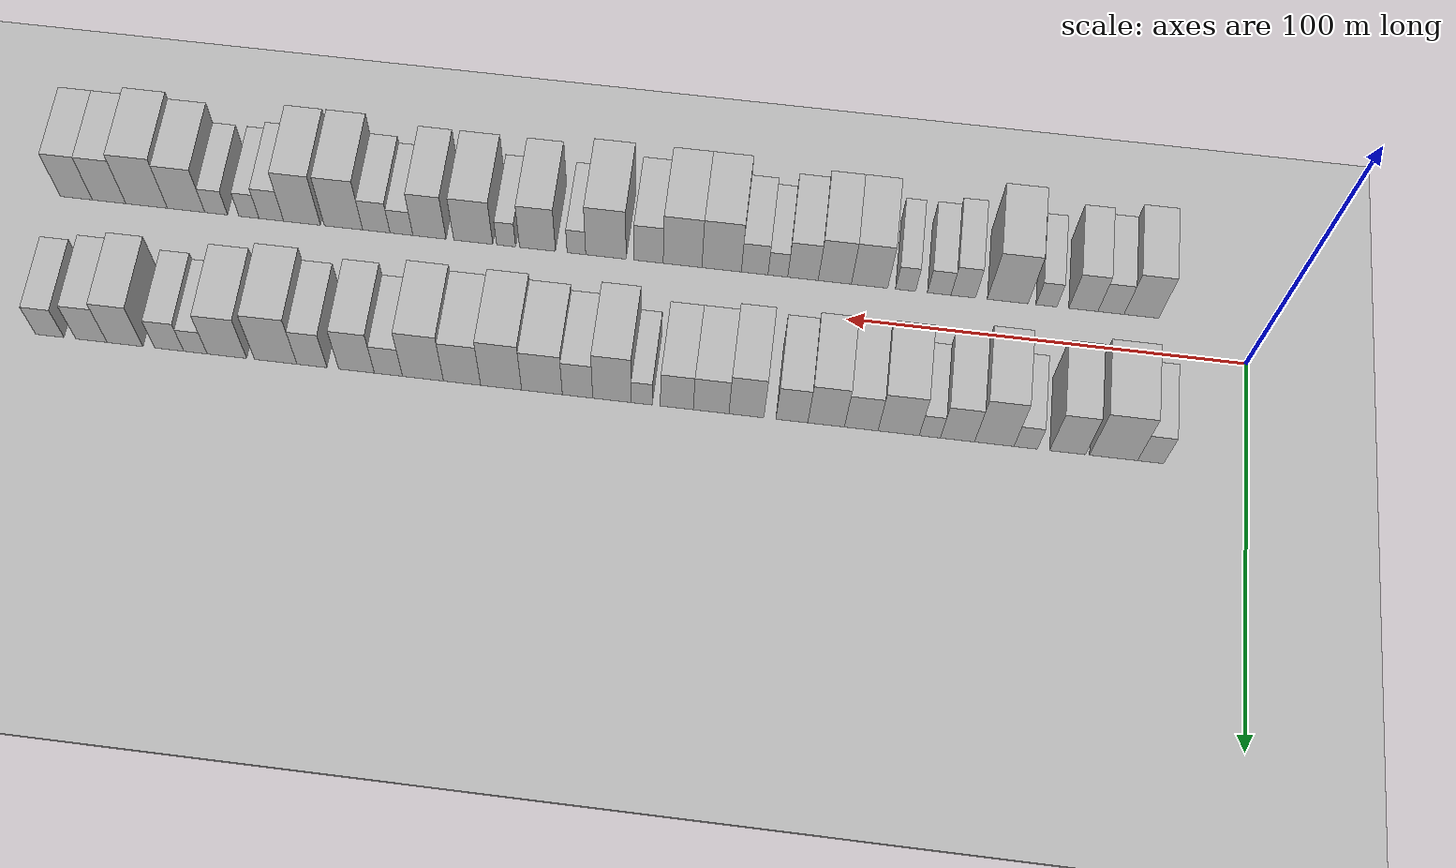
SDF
<?xml version="1.0" encoding="utf-8"?>

<sdf version="1.6">

   <world name="default">

      <gui fullscreen="0">

         <camera name="user_camera">

            <pose>-15 0 4.57585 0 0 0</pose>

            <view_controller>orbit</view_controller>

         </camera>

      </gui>

      <scene>

         <sky>

           <clouds>

             <speed>12</speed>

           </clouds>

         </sky>

         <ambient>0.4 0.4 0.4 1</ambient>

         <background>0.7 0.7 0.7 1</background>

         <shadows>1</shadows>

      </scene>

      <gravity>0 0 -9.8066</gravity>

      <magnetic_field>6e-06 2.3e-05 -4.2e-05</magnetic_field>

      <physics default="0" name="default_physics" type="ode">

         <ode>

            <solver>

               <type>quick</type>

               <iters>10</iters>

               <sor>1.0</sor>

               <use_dynamic_moi_rescaling>0</use_dynamic_moi_rescaling>

            </solver>

            <constraints>

               <cfm>0</cfm>

               <erp>0.2</erp>

               <contact_max_correcting_vel>100</contact_max_correcting_vel>

               <contact_surface_layer>0.001</contact_surface_layer>

            </constraints>

         </ode>

         <max_step_size>0.004</max_step_size>

         <real_time_factor>1</real_time_factor>

         <real_time_update_rate>250</real_time_update_rate>

      </physics>

      <light name="sun" type="directional">

         <cast_shadows>1</cast_shadows>

         <pose>0 0 10 0 0 0</pose>

         <diffuse>0.8 0.8 0.8 1</diffuse>

         <specular>0.2 0.2 0.2 1</specular>

         <attenuation>

            <range>1000</range>

            <constant>0.9</constant>

            <linear>0.01</linear>

            <quadratic>0.001</quadratic>

         </attenuation>

         <direction>-0.5 0.1 -0.9</direction>

      </light>

      <include>

         <name>ground_plane_1</name>

         <uri>model://HANNAS_ground_plane</uri>

         <pose>0 0 0  0 0 0</pose>

      </include>

      <include>

         <name>ground_plane_2</name>

         <uri>model://HANNAS_ground_plane</uri>

         <pose>100 0 0  0 0 0</pose>

      </include>

      <model name="building_1">

         <static>1</static>

         <pose frame="">23.1805 20.0000 0 0.000000 0.000000 1.570796</pose>

         <link name="link">

            <pose frame="">0 0 7.50 0 0 0</pose>

            <collision name="collision">

               <geometry>

                  <box>

                     <size>20.0000 6.3611 15.0000</size>

                  </box>

               </geometry>

               <max_contacts>10</max_contacts>

               <surface>

                  <contact>

                     <ode/>

                  </contact>

                  <bounce/>

                  <friction>

                     <torsional>

                        <ode/>

                     </torsional>

                     <ode/>

                  </friction>

               </surface>

            </collision>

            <visual name="visual">

               <cast_shadows>0</cast_shadows>

               <geometry>

                  <box>

                     <size>20.0000 6.3611 15.0000</size>

                  </box>

               </geometry>

               <material>

                  <script>

                     <uri>model://HANNAS_wall/materials/scripts</uri>

                     <uri>model://HANNAS_wall/materials/textures</uri>

                     <name>vrc/HANNAS_wall</name>

                  </script>

               </material>

            </visual>

            <self_collide>0</self_collide>

            <enable_wind>0</enable_wind>

            <kinematic>0</kinematic>

         </link>

      </model>

      <model name="building_2">

         <static>1</static>

         <pose frame="">32.2111 20.0000 0 0.000000 0.000000 1.570796</pose>

         <link name="link">

            <pose frame="">0 0 12.00 0 0 0</pose>

            <collision name="collision">

               <geometry>

                  <box>

                     <size>20.0000 11.7001 24.0000</size>

                  </box>

               </geometry>

               <max_contacts>10</max_contacts>

               <surface>

                  <contact>

                     <ode/>

                  </contact>

                  <bounce/>

                  <friction>

                     <torsional>

                        <ode/>

                     </torsional>

                     <ode/>

                  </friction>

               </surface>

            </collision>

            <visual name="visual">

               <cast_shadows>0</cast_shadows>

               <geometry>

                  <box>

                     <size>20.0000 11.7001 24.0000</size>

                  </box>

               </geometry>

               <material>

                  <script>

                     <uri>model://HANNAS_wall/materials/scripts</uri>

                     <uri>model://HANNAS_wall/materials/textures</uri>

                     <name>vrc/HANNAS_wall</name>

                  </script>

               </material>

            </visual>

            <self_collide>0</self_collide>

            <enable_wind>0</enable_wind>

            <kinematic>0</kinematic>

         </link>

      </model>

      <model name="building_3">

         <static>1</static>

         <pose frame="">43.4229 20.0000 0 0.000000 0.000000 1.570796</pose>

         <link name="link">

            <pose frame="">0 0 10.50 0 0 0</pose>

            <collision name="collision">

               <geometry>

                  <box>

                     <size>20.0000 8.7235 21.0000</size>

                  </box>

               </geometry>

               <max_contacts>10</max_contacts>

               <surface>

                  <contact>

                     <ode/>

                  </contact>

                  <bounce/>

                  <friction>

                     <torsional>

                        <ode/>

                     </torsional>

                     <ode/>

                  </friction>

               </surface>

            </collision>

            <visual name="visual">

               <cast_shadows>0</cast_shadows>

               <geometry>

                  <box>

                     <size>20.0000 8.7235 21.0000</size>

                  </box>

               </geometry>

               <material>

                  <script>

                     <uri>model://HANNAS_wall/materials/scripts</uri>

                     <uri>model://HANNAS_wall/materials/textures</uri>

                     <name>vrc/HANNAS_wall</name>

                  </script>

               </material>

            </visual>

            <self_collide>0</self_collide>

            <enable_wind>0</enable_wind>

            <kinematic>0</kinematic>

         </link>

      </model>

      <model name="building_4">

         <static>1</static>

         <pose frame="">53.6383 20.0000 0 0.000000 0.000000 1.570796</pose>

         <link name="link">

            <pose frame="">0 0 6.00 0 0 0</pose>

            <collision name="collision">

               <geometry>

                  <box>

                     <size>20.0000 5.7074 12.0000</size>

                  </box>

               </geometry>

               <max_contacts>10</max_contacts>

               <surface>

                  <contact>

                     <ode/>

                  </contact>

                  <bounce/>

                  <friction>

                     <torsional>

                        <ode/>

                     </torsional>

                     <ode/>

                  </friction>

               </surface>

            </collision>

            <visual name="visual">

               <cast_shadows>0</cast_shadows>

               <geometry>

                  <box>

                     <size>20.0000 5.7074 12.0000</size>

                  </box>

               </geometry>

               <material>

                  <script>

                     <uri>model://HANNAS_wall/materials/scripts</uri>

                     <uri>model://HANNAS_wall/materials/textures</uri>

                     <name>vrc/HANNAS_wall</name>

                  </script>

               </material>

            </visual>

            <self_collide>0</self_collide>

            <enable_wind>0</enable_wind>

            <kinematic>0</kinematic>

         </link>

      </model>

      <model name="building_5">

         <static>1</static>

         <pose frame="">61.3309 20.0000 0 0.000000 0.000000 1.570796</pose>

         <link name="link">

            <pose frame="">0 0 12.00 0 0 0</pose>

            <collision name="collision">

               <geometry>

                  <box>

                     <size>20.0000 9.6777 24.0000</size>

                  </box>

               </geometry>

               <max_contacts>10</max_contacts>

               <surface>

                  <contact>

                     <ode/>

                  </contact>

                  <bounce/>

                  <friction>

                     <torsional>

                        <ode/>

                     </torsional>

                     <ode/>

                  </friction>

               </surface>

            </collision>

            <visual name="visual">

               <cast_shadows>0</cast_shadows>

               <geometry>

                  <box>

                     <size>20.0000 9.6777 24.0000</size>

                  </box>

               </geometry>

               <material>

                  <script>

                     <uri>model://HANNAS_wall/materials/scripts</uri>

                     <uri>model://HANNAS_wall/materials/textures</uri>

                     <name>vrc/HANNAS_wall</name>

                  </script>

               </material>

            </visual>

            <self_collide>0</self_collide>

            <enable_wind>0</enable_wind>

            <kinematic>0</kinematic>

         </link>

      </model>

      <model name="building_6">

         <static>1</static>

         <pose frame="">70.3550 20.0000 0 0.000000 0.000000 1.570796</pose>

         <link name="link">

            <pose frame="">0 0 9.00 0 0 0</pose>

            <collision name="collision">

               <geometry>

                  <box>

                     <size>20.0000 8.3705 18.0000</size>

                  </box>

               </geometry>

               <max_contacts>10</max_contacts>

               <surface>

                  <contact>

                     <ode/>

                  </contact>

                  <bounce/>

                  <friction>

                     <torsional>

                        <ode/>

                     </torsional>

                     <ode/>

                  </friction>

               </surface>

            </collision>

            <visual name="visual">

               <cast_shadows>0</cast_shadows>

               <geometry>

                  <box>

                     <size>20.0000 8.3705 18.0000</size>

                  </box>

               </geometry>

               <material>

                  <script>

                     <uri>model://HANNAS_wall/materials/scripts</uri>

                     <uri>model://HANNAS_wall/materials/textures</uri>

                     <name>vrc/HANNAS_wall</name>

                  </script>

               </material>

            </visual>

            <self_collide>0</self_collide>

            <enable_wind>0</enable_wind>

            <kinematic>0</kinematic>

         </link>

      </model>

      <model name="building_7">

         <static>1</static>

         <pose frame="">77.1355 20.0000 0 0.000000 0.000000 1.570796</pose>

         <link name="link">

            <pose frame="">0 0 6.00 0 0 0</pose>

            <collision name="collision">

               <geometry>

                  <box>

                     <size>20.0000 5.1903 12.0000</size>

                  </box>

               </geometry>

               <max_contacts>10</max_contacts>

               <surface>

                  <contact>

                     <ode/>

                  </contact>

                  <bounce/>

                  <friction>

                     <torsional>

                        <ode/>

                     </torsional>

                     <ode/>

                  </friction>

               </surface>

            </collision>

            <visual name="visual">

               <cast_shadows>0</cast_shadows>

               <geometry>

                  <box>

                     <size>20.0000 5.1903 12.0000</size>

                  </box>

               </geometry>

               <material>

                  <script>

                     <uri>model://HANNAS_wall/materials/scripts</uri>

                     <uri>model://HANNAS_wall/materials/textures</uri>

                     <name>vrc/HANNAS_wall</name>

                  </script>

               </material>

            </visual>

            <self_collide>0</self_collide>

            <enable_wind>0</enable_wind>

            <kinematic>0</kinematic>

         </link>

      </model>

      <model name="building_8">

         <static>1</static>

         <pose frame="">84.8151 20.0000 0 0.000000 0.000000 1.570796</pose>

         <link name="link">

            <pose frame="">0 0 10.50 0 0 0</pose>

            <collision name="collision">

               <geometry>

                  <box>

                     <size>20.0000 10.1690 21.0000</size>

                  </box>

               </geometry>

               <max_contacts>10</max_contacts>

               <surface>

                  <contact>

                     <ode/>

                  </contact>

                  <bounce/>

                  <friction>

                     <torsional>

                        <ode/>

                     </torsional>

                     <ode/>

                  </friction>

               </surface>

            </collision>

            <visual name="visual">

               <cast_shadows>0</cast_shadows>

               <geometry>

                  <box>

                     <size>20.0000 10.1690 21.0000</size>

                  </box>

               </geometry>

               <material>

                  <script>

                     <uri>model://HANNAS_wall/materials/scripts</uri>

                     <uri>model://HANNAS_wall/materials/textures</uri>

                     <name>vrc/HANNAS_wall</name>

                  </script>

               </material>

            </visual>

            <self_collide>0</self_collide>

            <enable_wind>0</enable_wind>

            <kinematic>0</kinematic>

         </link>

      </model>

      <model name="building_9">

         <static>1</static>

         <pose frame="">94.0329 20.0000 0 0.000000 0.000000 1.570796</pose>

         <link name="link">

            <pose frame="">0 0 9.00 0 0 0</pose>

            <collision name="collision">

               <geometry>

                  <box>

                     <size>20.0000 8.2667 18.0000</size>

                  </box>

               </geometry>

               <max_contacts>10</max_contacts>

               <surface>

                  <contact>

                     <ode/>

                  </contact>

                  <bounce/>

                  <friction>

                     <torsional>

                        <ode/>

                     </torsional>

                     <ode/>

                  </friction>

               </surface>

            </collision>

            <visual name="visual">

               <cast_shadows>0</cast_shadows>

               <geometry>

                  <box>

                     <size>20.0000 8.2667 18.0000</size>

                  </box>

               </geometry>

               <material>

                  <script>

                     <uri>model://HANNAS_wall/materials/scripts</uri>

                     <uri>model://HANNAS_wall/materials/textures</uri>

                     <name>vrc/HANNAS_wall</name>

                  </script>

               </material>

            </visual>

            <self_collide>0</self_collide>

            <enable_wind>0</enable_wind>

            <kinematic>0</kinematic>

         </link>

      </model>

      <model name="building_10">

         <static>1</static>

         <pose frame="">102.6994 20.0000 0 0.000000 0.000000 1.570796</pose>

         <link name="link">

            <pose frame="">0 0 10.50 0 0 0</pose>

            <collision name="collision">

               <geometry>

                  <box>

                     <size>20.0000 9.0662 21.0000</size>

                  </box>

               </geometry>

               <max_contacts>10</max_contacts>

               <surface>

                  <contact>

                     <ode/>

                  </contact>

                  <bounce/>

                  <friction>

                     <torsional>

                        <ode/>

                     </torsional>

                     <ode/>

                  </friction>

               </surface>

            </collision>

            <visual name="visual">

               <cast_shadows>0</cast_shadows>

               <geometry>

                  <box>

                     <size>20.0000 9.0662 21.0000</size>

                  </box>

               </geometry>

               <material>

                  <script>

                     <uri>model://HANNAS_wall/materials/scripts</uri>

                     <uri>model://HANNAS_wall/materials/textures</uri>

                     <name>vrc/HANNAS_wall</name>

                  </script>

               </material>

            </visual>

            <self_collide>0</self_collide>

            <enable_wind>0</enable_wind>

            <kinematic>0</kinematic>

         </link>

      </model>

      <model name="building_11">

         <static>1</static>

         <pose frame="">111.1695 20.0000 0 0.000000 0.000000 1.570796</pose>

         <link name="link">

            <pose frame="">0 0 9.00 0 0 0</pose>

            <collision name="collision">

               <geometry>

                  <box>

                     <size>20.0000 7.8741 18.0000</size>

                  </box>

               </geometry>

               <max_contacts>10</max_contacts>

               <surface>

                  <contact>

                     <ode/>

                  </contact>

                  <bounce/>

                  <friction>

                     <torsional>

                        <ode/>

                     </torsional>

                     <ode/>

                  </friction>

               </surface>

            </collision>

            <visual name="visual">

               <cast_shadows>0</cast_shadows>

               <geometry>

                  <box>

                     <size>20.0000 7.8741 18.0000</size>

                  </box>

               </geometry>

               <material>

                  <script>

                     <uri>model://HANNAS_wall/materials/scripts</uri>

                     <uri>model://HANNAS_wall/materials/textures</uri>

                     <name>vrc/HANNAS_wall</name>

                  </script>

               </material>

            </visual>

            <self_collide>0</self_collide>

            <enable_wind>0</enable_wind>

            <kinematic>0</kinematic>

         </link>

      </model>

      <model name="building_12">

         <static>1</static>

         <pose frame="">122.4387 20.0000 0 0.000000 0.000000 1.570796</pose>

         <link name="link">

            <pose frame="">0 0 10.50 0 0 0</pose>

            <collision name="collision">

               <geometry>

                  <box>

                     <size>20.0000 8.6643 21.0000</size>

                  </box>

               </geometry>

               <max_contacts>10</max_contacts>

               <surface>

                  <contact>

                     <ode/>

                  </contact>

                  <bounce/>

                  <friction>

                     <torsional>

                        <ode/>

                     </torsional>

                     <ode/>

                  </friction>

               </surface>

            </collision>

            <visual name="visual">

               <cast_shadows>0</cast_shadows>

               <geometry>

                  <box>

                     <size>20.0000 8.6643 21.0000</size>

                  </box>

               </geometry>

               <material>

                  <script>

                     <uri>model://HANNAS_wall/materials/scripts</uri>

                     <uri>model://HANNAS_wall/materials/textures</uri>

                     <name>vrc/HANNAS_wall</name>

                  </script>

               </material>

            </visual>

            <self_collide>0</self_collide>

            <enable_wind>0</enable_wind>

            <kinematic>0</kinematic>

         </link>

      </model>

      <model name="building_13">

         <static>1</static>

         <pose frame="">131.1931 20.0000 0 0.000000 0.000000 1.570796</pose>

         <link name="link">

            <pose frame="">0 0 9.00 0 0 0</pose>

            <collision name="collision">

               <geometry>

                  <box>

                     <size>20.0000 8.8445 18.0000</size>

                  </box>

               </geometry>

               <max_contacts>10</max_contacts>

               <surface>

                  <contact>

                     <ode/>

                  </contact>

                  <bounce/>

                  <friction>

                     <torsional>

                        <ode/>

                     </torsional>

                     <ode/>

                  </friction>

               </surface>

            </collision>

            <visual name="visual">

               <cast_shadows>0</cast_shadows>

               <geometry>

                  <box>

                     <size>20.0000 8.8445 18.0000</size>

                  </box>

               </geometry>

               <material>

                  <script>

                     <uri>model://HANNAS_wall/materials/scripts</uri>

                     <uri>model://HANNAS_wall/materials/textures</uri>

                     <name>vrc/HANNAS_wall</name>

                  </script>

               </material>

            </visual>

            <self_collide>0</self_collide>

            <enable_wind>0</enable_wind>

            <kinematic>0</kinematic>

         </link>

      </model>

      <model name="building_14">

         <static>1</static>

         <pose frame="">139.7270 20.0000 0 0.000000 0.000000 1.570796</pose>

         <link name="link">

            <pose frame="">0 0 9.00 0 0 0</pose>

            <collision name="collision">

               <geometry>

                  <box>

                     <size>20.0000 8.2233 18.0000</size>

                  </box>

               </geometry>

               <max_contacts>10</max_contacts>

               <surface>

                  <contact>

                     <ode/>

                  </contact>

                  <bounce/>

                  <friction>

                     <torsional>

                        <ode/>

                     </torsional>

                     <ode/>

                  </friction>

               </surface>

            </collision>

            <visual name="visual">

               <cast_shadows>0</cast_shadows>

               <geometry>

                  <box>

                     <size>20.0000 8.2233 18.0000</size>

                  </box>

               </geometry>

               <material>

                  <script>

                     <uri>model://HANNAS_wall/materials/scripts</uri>

                     <uri>model://HANNAS_wall/materials/textures</uri>

                     <name>vrc/HANNAS_wall</name>

                  </script>

               </material>

            </visual>

            <self_collide>0</self_collide>

            <enable_wind>0</enable_wind>

            <kinematic>0</kinematic>

         </link>

      </model>

      <model name="building_15">

         <static>1</static>

         <pose frame="">148.4612 20.0000 0 0.000000 0.000000 1.570796</pose>

         <link name="link">

            <pose frame="">0 0 6.00 0 0 0</pose>

            <collision name="collision">

               <geometry>

                  <box>

                     <size>20.0000 5.2451 12.0000</size>

                  </box>

               </geometry>

               <max_contacts>10</max_contacts>

               <surface>

                  <contact>

                     <ode/>

                  </contact>

                  <bounce/>

                  <friction>

                     <torsional>

                        <ode/>

                     </torsional>

                     <ode/>

                  </friction>

               </surface>

            </collision>

            <visual name="visual">

               <cast_shadows>0</cast_shadows>

               <geometry>

                  <box>

                     <size>20.0000 5.2451 12.0000</size>

                  </box>

               </geometry>

               <material>

                  <script>

                     <uri>model://HANNAS_wall/materials/scripts</uri>

                     <uri>model://HANNAS_wall/materials/textures</uri>

                     <name>vrc/HANNAS_wall</name>

                  </script>

               </material>

            </visual>

            <self_collide>0</self_collide>

            <enable_wind>0</enable_wind>

            <kinematic>0</kinematic>

         </link>

      </model>

      <model name="building_16">

         <static>1</static>

         <pose frame="">155.8896 20.0000 0 0.000000 0.000000 1.570796</pose>

         <link name="link">

            <pose frame="">0 0 12.00 0 0 0</pose>

            <collision name="collision">

               <geometry>

                  <box>

                     <size>20.0000 9.6118 24.0000</size>

                  </box>

               </geometry>

               <max_contacts>10</max_contacts>

               <surface>

                  <contact>

                     <ode/>

                  </contact>

                  <bounce/>

                  <friction>

                     <torsional>

                        <ode/>

                     </torsional>

                     <ode/>

                  </friction>

               </surface>

            </collision>

            <visual name="visual">

               <cast_shadows>0</cast_shadows>

               <geometry>

                  <box>

                     <size>20.0000 9.6118 24.0000</size>

                  </box>

               </geometry>

               <material>

                  <script>

                     <uri>model://HANNAS_wall/materials/scripts</uri>

                     <uri>model://HANNAS_wall/materials/textures</uri>

                     <name>vrc/HANNAS_wall</name>

                  </script>

               </material>

            </visual>

            <self_collide>0</self_collide>

            <enable_wind>0</enable_wind>

            <kinematic>0</kinematic>

         </link>

      </model>

      <model name="building_17">

         <static>1</static>

         <pose frame="">164.4881 20.0000 0 0.000000 0.000000 1.570796</pose>

         <link name="link">

            <pose frame="">0 0 9.00 0 0 0</pose>

            <collision name="collision">

               <geometry>

                  <box>

                     <size>20.0000 7.5852 18.0000</size>

                  </box>

               </geometry>

               <max_contacts>10</max_contacts>

               <surface>

                  <contact>

                     <ode/>

                  </contact>

                  <bounce/>

                  <friction>

                     <torsional>

                        <ode/>

                     </torsional>

                     <ode/>

                  </friction>

               </surface>

            </collision>

            <visual name="visual">

               <cast_shadows>0</cast_shadows>

               <geometry>

                  <box>

                     <size>20.0000 7.5852 18.0000</size>

                  </box>

               </geometry>

               <material>

                  <script>

                     <uri>model://HANNAS_wall/materials/scripts</uri>

                     <uri>model://HANNAS_wall/materials/textures</uri>

                     <name>vrc/HANNAS_wall</name>

                  </script>

               </material>

            </visual>

            <self_collide>0</self_collide>

            <enable_wind>0</enable_wind>

            <kinematic>0</kinematic>

         </link>

      </model>

      <model name="building_18">

         <static>1</static>

         <pose frame="">173.3869 20.0000 0 0.000000 0.000000 1.570796</pose>

         <link name="link">

            <pose frame="">0 0 10.50 0 0 0</pose>

            <collision name="collision">

               <geometry>

                  <box>

                     <size>20.0000 10.2125 21.0000</size>

                  </box>

               </geometry>

               <max_contacts>10</max_contacts>

               <surface>

                  <contact>

                     <ode/>

                  </contact>

                  <bounce/>

                  <friction>

                     <torsional>

                        <ode/>

                     </torsional>

                     <ode/>

                  </friction>

               </surface>

            </collision>

            <visual name="visual">

               <cast_shadows>0</cast_shadows>

               <geometry>

                  <box>

                     <size>20.0000 10.2125 21.0000</size>

                  </box>

               </geometry>

               <material>

                  <script>

                     <uri>model://HANNAS_wall/materials/scripts</uri>

                     <uri>model://HANNAS_wall/materials/textures</uri>

                     <name>vrc/HANNAS_wall</name>

                  </script>

               </material>

            </visual>

            <self_collide>0</self_collide>

            <enable_wind>0</enable_wind>

            <kinematic>0</kinematic>

         </link>

      </model>

      <model name="building_19">

         <static>1</static>

         <pose frame="">183.6347 20.0000 0 0.000000 0.000000 1.570796</pose>

         <link name="link">

            <pose frame="">0 0 12.00 0 0 0</pose>

            <collision name="collision">

               <geometry>

                  <box>

                     <size>20.0000 10.2831 24.0000</size>

                  </box>

               </geometry>

               <max_contacts>10</max_contacts>

               <surface>

                  <contact>

                     <ode/>

                  </contact>

                  <bounce/>

                  <friction>

                     <torsional>

                        <ode/>

                     </torsional>

                     <ode/>

                  </friction>

               </surface>

            </collision>

            <visual name="visual">

               <cast_shadows>0</cast_shadows>

               <geometry>

                  <box>

                     <size>20.0000 10.2831 24.0000</size>

                  </box>

               </geometry>

               <material>

                  <script>

                     <uri>model://HANNAS_wall/materials/scripts</uri>

                     <uri>model://HANNAS_wall/materials/textures</uri>

                     <name>vrc/HANNAS_wall</name>

                  </script>

               </material>

            </visual>

            <self_collide>0</self_collide>

            <enable_wind>0</enable_wind>

            <kinematic>0</kinematic>

         </link>

      </model>

      <model name="building_20">

         <static>1</static>

         <pose frame="">193.4591 20.0000 0 0.000000 0.000000 1.570796</pose>

         <link name="link">

            <pose frame="">0 0 10.50 0 0 0</pose>

            <collision name="collision">

               <geometry>

                  <box>

                     <size>20.0000 9.3656 21.0000</size>

                  </box>

               </geometry>

               <max_contacts>10</max_contacts>

               <surface>

                  <contact>

                     <ode/>

                  </contact>

                  <bounce/>

                  <friction>

                     <torsional>

                        <ode/>

                     </torsional>

                     <ode/>

                  </friction>

               </surface>

            </collision>

            <visual name="visual">

               <cast_shadows>0</cast_shadows>

               <geometry>

                  <box>

                     <size>20.0000 9.3656 21.0000</size>

                  </box>

               </geometry>

               <material>

                  <script>

                     <uri>model://HANNAS_wall/materials/scripts</uri>

                     <uri>model://HANNAS_wall/materials/textures</uri>

                     <name>vrc/HANNAS_wall</name>

                  </script>

               </material>

            </visual>

            <self_collide>0</self_collide>

            <enable_wind>0</enable_wind>

            <kinematic>0</kinematic>

         </link>

      </model>

      <model name="building_21">

         <static>1</static>

         <pose frame="">203.3100 20.0000 0 0.000000 0.000000 1.570796</pose>

         <link name="link">

            <pose frame="">0 0 12.00 0 0 0</pose>

            <collision name="collision">

               <geometry>

                  <box>

                     <size>20.0000 10.3362 24.0000</size>

                  </box>

               </geometry>

               <max_contacts>10</max_contacts>

               <surface>

                  <contact>

                     <ode/>

                  </contact>

                  <bounce/>

                  <friction>

                     <torsional>

                        <ode/>

                     </torsional>

                     <ode/>

                  </friction>

               </surface>

            </collision>

            <visual name="visual">

               <cast_shadows>0</cast_shadows>

               <geometry>

                  <box>

                     <size>20.0000 10.3362 24.0000</size>

                  </box>

               </geometry>

               <material>

                  <script>

                     <uri>model://HANNAS_wall/materials/scripts</uri>

                     <uri>model://HANNAS_wall/materials/textures</uri>

                     <name>vrc/HANNAS_wall</name>

                  </script>

               </material>

            </visual>

            <self_collide>0</self_collide>

            <enable_wind>0</enable_wind>

            <kinematic>0</kinematic>

         </link>

      </model>

      <model name="building_22">

         <static>1</static>

         <pose frame="">212.0211 20.0000 0 0.000000 0.000000 1.570796</pose>

         <link name="link">

            <pose frame="">0 0 7.50 0 0 0</pose>

            <collision name="collision">

               <geometry>

                  <box>

                     <size>20.0000 7.0859 15.0000</size>

                  </box>

               </geometry>

               <max_contacts>10</max_contacts>

               <surface>

                  <contact>

                     <ode/>

                  </contact>

                  <bounce/>

                  <friction>

                     <torsional>

                        <ode/>

                     </torsional>

                     <ode/>

                  </friction>

               </surface>

            </collision>

            <visual name="visual">

               <cast_shadows>0</cast_shadows>

               <geometry>

                  <box>

                     <size>20.0000 7.0859 15.0000</size>

                  </box>

               </geometry>

               <material>

                  <script>

                     <uri>model://HANNAS_wall/materials/scripts</uri>

                     <uri>model://HANNAS_wall/materials/textures</uri>

                     <name>vrc/HANNAS_wall</name>

                  </script>

               </material>

            </visual>

            <self_collide>0</self_collide>

            <enable_wind>0</enable_wind>

            <kinematic>0</kinematic>

         </link>

      </model>

      <model name="building_23">

         <static>1</static>

         <pose frame="">220.0758 20.0000 0 0.000000 0.000000 1.570796</pose>

         <link name="link">

            <pose frame="">0 0 10.50 0 0 0</pose>

            <collision name="collision">

               <geometry>

                  <box>

                     <size>20.0000 9.0235 21.0000</size>

                  </box>

               </geometry>

               <max_contacts>10</max_contacts>

               <surface>

                  <contact>

                     <ode/>

                  </contact>

                  <bounce/>

                  <friction>

                     <torsional>

                        <ode/>

                     </torsional>

                     <ode/>

                  </friction>

               </surface>

            </collision>

            <visual name="visual">

               <cast_shadows>0</cast_shadows>

               <geometry>

                  <box>

                     <size>20.0000 9.0235 21.0000</size>

                  </box>

               </geometry>

               <material>

                  <script>

                     <uri>model://HANNAS_wall/materials/scripts</uri>

                     <uri>model://HANNAS_wall/materials/textures</uri>

                     <name>vrc/HANNAS_wall</name>

                  </script>

               </material>

            </visual>

            <self_collide>0</self_collide>

            <enable_wind>0</enable_wind>

            <kinematic>0</kinematic>

         </link>

      </model>

      <model name="building_24">

         <static>1</static>

         <pose frame="">231.3806 20.0000 0 0.000000 0.000000 1.570796</pose>

         <link name="link">

            <pose frame="">0 0 9.00 0 0 0</pose>

            <collision name="collision">

               <geometry>

                  <box>

                     <size>20.0000 7.5862 18.0000</size>

                  </box>

               </geometry>

               <max_contacts>10</max_contacts>

               <surface>

                  <contact>

                     <ode/>

                  </contact>

                  <bounce/>

                  <friction>

                     <torsional>

                        <ode/>

                     </torsional>

                     <ode/>

                  </friction>

               </surface>

            </collision>

            <visual name="visual">

               <cast_shadows>0</cast_shadows>

               <geometry>

                  <box>

                     <size>20.0000 7.5862 18.0000</size>

                  </box>

               </geometry>

               <material>

                  <script>

                     <uri>model://HANNAS_wall/materials/scripts</uri>

                     <uri>model://HANNAS_wall/materials/textures</uri>

                     <name>vrc/HANNAS_wall</name>

                  </script>

               </material>

            </visual>

            <self_collide>0</self_collide>

            <enable_wind>0</enable_wind>

            <kinematic>0</kinematic>

         </link>

      </model>

      <model name="building_25">

         <static>1</static>

         <pose frame="">240.5744 20.0000 0 0.000000 0.000000 1.570796</pose>

         <link name="link">

            <pose frame="">0 0 12.00 0 0 0</pose>

            <collision name="collision">

               <geometry>

                  <box>

                     <size>20.0000 10.8014 24.0000</size>

                  </box>

               </geometry>

               <max_contacts>10</max_contacts>

               <surface>

                  <contact>

                     <ode/>

                  </contact>

                  <bounce/>

                  <friction>

                     <torsional>

                        <ode/>

                     </torsional>

                     <ode/>

                  </friction>

               </surface>

            </collision>

            <visual name="visual">

               <cast_shadows>0</cast_shadows>

               <geometry>

                  <box>

                     <size>20.0000 10.8014 24.0000</size>

                  </box>

               </geometry>

               <material>

                  <script>

                     <uri>model://HANNAS_wall/materials/scripts</uri>

                     <uri>model://HANNAS_wall/materials/textures</uri>

                     <name>vrc/HANNAS_wall</name>

                  </script>

               </material>

            </visual>

            <self_collide>0</self_collide>

            <enable_wind>0</enable_wind>

            <kinematic>0</kinematic>

         </link>

      </model>

      <model name="building_26">

         <static>1</static>

         <pose frame="">252.9992 20.0000 0 0.000000 0.000000 1.570796</pose>

         <link name="link">

            <pose frame="">0 0 10.50 0 0 0</pose>

            <collision name="collision">

               <geometry>

                  <box>

                     <size>20.0000 10.0482 21.0000</size>

                  </box>

               </geometry>

               <max_contacts>10</max_contacts>

               <surface>

                  <contact>

                     <ode/>

                  </contact>

                  <bounce/>

                  <friction>

                     <torsional>

                        <ode/>

                     </torsional>

                     <ode/>

                  </friction>

               </surface>

            </collision>

            <visual name="visual">

               <cast_shadows>0</cast_shadows>

               <geometry>

                  <box>

                     <size>20.0000 10.0482 21.0000</size>

                  </box>

               </geometry>

               <material>

                  <script>

                     <uri>model://HANNAS_wall/materials/scripts</uri>

                     <uri>model://HANNAS_wall/materials/textures</uri>

                     <name>vrc/HANNAS_wall</name>

                  </script>

               </material>

            </visual>

            <self_collide>0</self_collide>

            <enable_wind>0</enable_wind>

            <kinematic>0</kinematic>

         </link>

      </model>

      <model name="building_27">

         <static>1</static>

         <pose frame="">261.0181 20.0000 0 0.000000 0.000000 1.570796</pose>

         <link name="link">

            <pose frame="">0 0 6.00 0 0 0</pose>

            <collision name="collision">

               <geometry>

                  <box>

                     <size>20.0000 5.9895 12.0000</size>

                  </box>

               </geometry>

               <max_contacts>10</max_contacts>

               <surface>

                  <contact>

                     <ode/>

                  </contact>

                  <bounce/>

                  <friction>

                     <torsional>

                        <ode/>

                     </torsional>

                     <ode/>

                  </friction>

               </surface>

            </collision>

            <visual name="visual">

               <cast_shadows>0</cast_shadows>

               <geometry>

                  <box>

                     <size>20.0000 5.9895 12.0000</size>

                  </box>

               </geometry>

               <material>

                  <script>

                     <uri>model://HANNAS_wall/materials/scripts</uri>

                     <uri>model://HANNAS_wall/materials/textures</uri>

                     <name>vrc/HANNAS_wall</name>

                  </script>

               </material>

            </visual>

            <self_collide>0</self_collide>

            <enable_wind>0</enable_wind>

            <kinematic>0</kinematic>

         </link>

      </model>

      <model name="building_28">

         <static>1</static>

         <pose frame="">267.7192 20.0000 0 0.000000 0.000000 1.570796</pose>

         <link name="link">

            <pose frame="">0 0 7.50 0 0 0</pose>

            <collision name="collision">

               <geometry>

                  <box>

                     <size>20.0000 7.4128 15.0000</size>

                  </box>

               </geometry>

               <max_contacts>10</max_contacts>

               <surface>

                  <contact>

                     <ode/>

                  </contact>

                  <bounce/>

                  <friction>

                     <torsional>

                        <ode/>

                     </torsional>

                     <ode/>

                  </friction>

               </surface>

            </collision>

            <visual name="visual">

               <cast_shadows>0</cast_shadows>

               <geometry>

                  <box>

                     <size>20.0000 7.4128 15.0000</size>

                  </box>

               </geometry>

               <material>

                  <script>

                     <uri>model://HANNAS_wall/materials/scripts</uri>

                     <uri>model://HANNAS_wall/materials/textures</uri>

                     <name>vrc/HANNAS_wall</name>

                  </script>

               </material>

            </visual>

            <self_collide>0</self_collide>

            <enable_wind>0</enable_wind>

            <kinematic>0</kinematic>

         </link>

      </model>

      <model name="building_29">

         <static>1</static>

         <pose frame="">279.0179 20.0000 0 0.000000 0.000000 1.570796</pose>

         <link name="link">

            <pose frame="">0 0 10.50 0 0 0</pose>

            <collision name="collision">

               <geometry>

                  <box>

                     <size>20.0000 9.1847 21.0000</size>

                  </box>

               </geometry>

               <max_contacts>10</max_contacts>

               <surface>

                  <contact>

                     <ode/>

                  </contact>

                  <bounce/>

                  <friction>

                     <torsional>

                        <ode/>

                     </torsional>

                     <ode/>

                  </friction>

               </surface>

            </collision>

            <visual name="visual">

               <cast_shadows>0</cast_shadows>

               <geometry>

                  <box>

                     <size>20.0000 9.1847 21.0000</size>

                  </box>

               </geometry>

               <material>

                  <script>

                     <uri>model://HANNAS_wall/materials/scripts</uri>

                     <uri>model://HANNAS_wall/materials/textures</uri>

                     <name>vrc/HANNAS_wall</name>

                  </script>

               </material>

            </visual>

            <self_collide>0</self_collide>

            <enable_wind>0</enable_wind>

            <kinematic>0</kinematic>

         </link>

      </model>

      <model name="building_30">

         <static>1</static>

         <pose frame="">287.6468 20.0000 0 0.000000 0.000000 1.570796</pose>

         <link name="link">

            <pose frame="">0 0 9.00 0 0 0</pose>

            <collision name="collision">

               <geometry>

                  <box>

                     <size>20.0000 8.0731 18.0000</size>

                  </box>

               </geometry>

               <max_contacts>10</max_contacts>

               <surface>

                  <contact>

                     <ode/>

                  </contact>

                  <bounce/>

                  <friction>

                     <torsional>

                        <ode/>

                     </torsional>

                     <ode/>

                  </friction>

               </surface>

            </collision>

            <visual name="visual">

               <cast_shadows>0</cast_shadows>

               <geometry>

                  <box>

                     <size>20.0000 8.0731 18.0000</size>

                  </box>

               </geometry>

               <material>

                  <script>

                     <uri>model://HANNAS_wall/materials/scripts</uri>

                     <uri>model://HANNAS_wall/materials/textures</uri>

                     <name>vrc/HANNAS_wall</name>

                  </script>

               </material>

            </visual>

            <self_collide>0</self_collide>

            <enable_wind>0</enable_wind>

            <kinematic>0</kinematic>

         </link>

      </model>

      <model name="building_31">

         <static>1</static>

         <pose frame="">298.3227 20.0000 0 0.000000 0.000000 1.570796</pose>

         <link name="link">

            <pose frame="">0 0 7.50 0 0 0</pose>

            <collision name="collision">

               <geometry>

                  <box>

                     <size>20.0000 7.2786 15.0000</size>

                  </box>

               </geometry>

               <max_contacts>10</max_contacts>

               <surface>

                  <contact>

                     <ode/>

                  </contact>

                  <bounce/>

                  <friction>

                     <torsional>

                        <ode/>

                     </torsional>

                     <ode/>

                  </friction>

               </surface>

            </collision>

            <visual name="visual">

               <cast_shadows>0</cast_shadows>

               <geometry>

                  <box>

                     <size>20.0000 7.2786 15.0000</size>

                  </box>

               </geometry>

               <material>

                  <script>

                     <uri>model://HANNAS_wall/materials/scripts</uri>

                     <uri>model://HANNAS_wall/materials/textures</uri>

                     <name>vrc/HANNAS_wall</name>

                  </script>

               </material>

            </visual>

            <self_collide>0</self_collide>

            <enable_wind>0</enable_wind>

            <kinematic>0</kinematic>

         </link>

      </model>

      <model name="building_32">

         <static>1</static>

         <pose frame="">26.3560 -20.0000 0 0.000000 0.000000 1.570796</pose>

         <link name="link">

            <pose frame="">0 0 10.50 0 0 0</pose>

            <collision name="collision">

               <geometry>

                  <box>

                     <size>20.0000 8.7120 21.0000</size>

                  </box>

               </geometry>

               <max_contacts>10</max_contacts>

               <surface>

                  <contact>

                     <ode/>

                  </contact>

                  <bounce/>

                  <friction>

                     <torsional>

                        <ode/>

                     </torsional>

                     <ode/>

                  </friction>

               </surface>

            </collision>

            <visual name="visual">

               <cast_shadows>0</cast_shadows>

               <geometry>

                  <box>

                     <size>20.0000 8.7120 21.0000</size>

                  </box>

               </geometry>

               <material>

                  <script>

                     <uri>model://HANNAS_wall/materials/scripts</uri>

                     <uri>model://HANNAS_wall/materials/textures</uri>

                     <name>vrc/HANNAS_wall</name>

                  </script>

               </material>

            </visual>

            <self_collide>0</self_collide>

            <enable_wind>0</enable_wind>

            <kinematic>0</kinematic>

         </link>

      </model>

      <model name="building_33">

         <static>1</static>

         <pose frame="">34.0038 -20.0000 0 0.000000 0.000000 1.570796</pose>

         <link name="link">

            <pose frame="">0 0 7.50 0 0 0</pose>

            <collision name="collision">

               <geometry>

                  <box>

                     <size>20.0000 6.5835 15.0000</size>

                  </box>

               </geometry>

               <max_contacts>10</max_contacts>

               <surface>

                  <contact>

                     <ode/>

                  </contact>

                  <bounce/>

                  <friction>

                     <torsional>

                        <ode/>

                     </torsional>

                     <ode/>

                  </friction>

               </surface>

            </collision>

            <visual name="visual">

               <cast_shadows>0</cast_shadows>

               <geometry>

                  <box>

                     <size>20.0000 6.5835 15.0000</size>

                  </box>

               </geometry>

               <material>

                  <script>

                     <uri>model://HANNAS_wall/materials/scripts</uri>

                     <uri>model://HANNAS_wall/materials/textures</uri>

                     <name>vrc/HANNAS_wall</name>

                  </script>

               </material>

            </visual>

            <self_collide>0</self_collide>

            <enable_wind>0</enable_wind>

            <kinematic>0</kinematic>

         </link>

      </model>

      <model name="building_34">

         <static>1</static>

         <pose frame="">40.9746 -20.0000 0 0.000000 0.000000 1.570796</pose>

         <link name="link">

            <pose frame="">0 0 9.00 0 0 0</pose>

            <collision name="collision">

               <geometry>

                  <box>

                     <size>20.0000 7.3580 18.0000</size>

                  </box>

               </geometry>

               <max_contacts>10</max_contacts>

               <surface>

                  <contact>

                     <ode/>

                  </contact>

                  <bounce/>

                  <friction>

                     <torsional>

                        <ode/>

                     </torsional>

                     <ode/>

                  </friction>

               </surface>

            </collision>

            <visual name="visual">

               <cast_shadows>0</cast_shadows>

               <geometry>

                  <box>

                     <size>20.0000 7.3580 18.0000</size>

                  </box>

               </geometry>

               <material>

                  <script>

                     <uri>model://HANNAS_wall/materials/scripts</uri>

                     <uri>model://HANNAS_wall/materials/textures</uri>

                     <name>vrc/HANNAS_wall</name>

                  </script>

               </material>

            </visual>

            <self_collide>0</self_collide>

            <enable_wind>0</enable_wind>

            <kinematic>0</kinematic>

         </link>

      </model>

      <model name="building_35">

         <static>1</static>

         <pose frame="">50.2781 -20.0000 0 0.000000 0.000000 1.570796</pose>

         <link name="link">

            <pose frame="">0 0 6.00 0 0 0</pose>

            <collision name="collision">

               <geometry>

                  <box>

                     <size>20.0000 5.2490 12.0000</size>

                  </box>

               </geometry>

               <max_contacts>10</max_contacts>

               <surface>

                  <contact>

                     <ode/>

                  </contact>

                  <bounce/>

                  <friction>

                     <torsional>

                        <ode/>

                     </torsional>

                     <ode/>

                  </friction>

               </surface>

            </collision>

            <visual name="visual">

               <cast_shadows>0</cast_shadows>

               <geometry>

                  <box>

                     <size>20.0000 5.2490 12.0000</size>

                  </box>

               </geometry>

               <material>

                  <script>

                     <uri>model://HANNAS_wall/materials/scripts</uri>

                     <uri>model://HANNAS_wall/materials/textures</uri>

                     <name>vrc/HANNAS_wall</name>

                  </script>

               </material>

            </visual>

            <self_collide>0</self_collide>

            <enable_wind>0</enable_wind>

            <kinematic>0</kinematic>

         </link>

      </model>

      <model name="building_36">

         <static>1</static>

         <pose frame="">60.0614 -20.0000 0 0.000000 0.000000 1.570796</pose>

         <link name="link">

            <pose frame="">0 0 12.00 0 0 0</pose>

            <collision name="collision">

               <geometry>

                  <box>

                     <size>20.0000 10.3177 24.0000</size>

                  </box>

               </geometry>

               <max_contacts>10</max_contacts>

               <surface>

                  <contact>

                     <ode/>

                  </contact>

                  <bounce/>

                  <friction>

                     <torsional>

                        <ode/>

                     </torsional>

                     <ode/>

                  </friction>

               </surface>

            </collision>

            <visual name="visual">

               <cast_shadows>0</cast_shadows>

               <geometry>

                  <box>

                     <size>20.0000 10.3177 24.0000</size>

                  </box>

               </geometry>

               <material>

                  <script>

                     <uri>model://HANNAS_wall/materials/scripts</uri>

                     <uri>model://HANNAS_wall/materials/textures</uri>

                     <name>vrc/HANNAS_wall</name>

                  </script>

               </material>

            </visual>

            <self_collide>0</self_collide>

            <enable_wind>0</enable_wind>

            <kinematic>0</kinematic>

         </link>

      </model>

      <model name="building_37">

         <static>1</static>

         <pose frame="">71.3219 -20.0000 0 0.000000 0.000000 1.570796</pose>

         <link name="link">

            <pose frame="">0 0 7.50 0 0 0</pose>

            <collision name="collision">

               <geometry>

                  <box>

                     <size>20.0000 6.2032 15.0000</size>

                  </box>

               </geometry>

               <max_contacts>10</max_contacts>

               <surface>

                  <contact>

                     <ode/>

                  </contact>

                  <bounce/>

                  <friction>

                     <torsional>

                        <ode/>

                     </torsional>

                     <ode/>

                  </friction>

               </surface>

            </collision>

            <visual name="visual">

               <cast_shadows>0</cast_shadows>

               <geometry>

                  <box>

                     <size>20.0000 6.2032 15.0000</size>

                  </box>

               </geometry>

               <material>

                  <script>

                     <uri>model://HANNAS_wall/materials/scripts</uri>

                     <uri>model://HANNAS_wall/materials/textures</uri>

                     <name>vrc/HANNAS_wall</name>

                  </script>

               </material>

            </visual>

            <self_collide>0</self_collide>

            <enable_wind>0</enable_wind>

            <kinematic>0</kinematic>

         </link>

      </model>

      <model name="building_38">

         <static>1</static>

         <pose frame="">77.4113 -20.0000 0 0.000000 0.000000 1.570796</pose>

         <link name="link">

            <pose frame="">0 0 6.00 0 0 0</pose>

            <collision name="collision">

               <geometry>

                  <box>

                     <size>20.0000 5.9757 12.0000</size>

                  </box>

               </geometry>

               <max_contacts>10</max_contacts>

               <surface>

                  <contact>

                     <ode/>

                  </contact>

                  <bounce/>

                  <friction>

                     <torsional>

                        <ode/>

                     </torsional>

                     <ode/>

                  </friction>

               </surface>

            </collision>

            <visual name="visual">

               <cast_shadows>0</cast_shadows>

               <geometry>

                  <box>

                     <size>20.0000 5.9757 12.0000</size>

                  </box>

               </geometry>

               <material>

                  <script>

                     <uri>model://HANNAS_wall/materials/scripts</uri>

                     <uri>model://HANNAS_wall/materials/textures</uri>

                     <name>vrc/HANNAS_wall</name>

                  </script>

               </material>

            </visual>

            <self_collide>0</self_collide>

            <enable_wind>0</enable_wind>

            <kinematic>0</kinematic>

         </link>

      </model>

      <model name="building_39">

         <static>1</static>

         <pose frame="">85.9588 -20.0000 0 0.000000 0.000000 1.570796</pose>

         <link name="link">

            <pose frame="">0 0 6.00 0 0 0</pose>

            <collision name="collision">

               <geometry>

                  <box>

                     <size>20.0000 5.1192 12.0000</size>

                  </box>

               </geometry>

               <max_contacts>10</max_contacts>

               <surface>

                  <contact>

                     <ode/>

                  </contact>

                  <bounce/>

                  <friction>

                     <torsional>

                        <ode/>

                     </torsional>

                     <ode/>

                  </friction>

               </surface>

            </collision>

            <visual name="visual">

               <cast_shadows>0</cast_shadows>

               <geometry>

                  <box>

                     <size>20.0000 5.1192 12.0000</size>

                  </box>

               </geometry>

               <material>

                  <script>

                     <uri>model://HANNAS_wall/materials/scripts</uri>

                     <uri>model://HANNAS_wall/materials/textures</uri>

                     <name>vrc/HANNAS_wall</name>

                  </script>

               </material>

            </visual>

            <self_collide>0</self_collide>

            <enable_wind>0</enable_wind>

            <kinematic>0</kinematic>

         </link>

      </model>

      <model name="building_40">

         <static>1</static>

         <pose frame="">95.1496 -20.0000 0 0.000000 0.000000 1.570796</pose>

         <link name="link">

            <pose frame="">0 0 10.50 0 0 0</pose>

            <collision name="collision">

               <geometry>

                  <box>

                     <size>20.0000 9.2623 21.0000</size>

                  </box>

               </geometry>

               <max_contacts>10</max_contacts>

               <surface>

                  <contact>

                     <ode/>

                  </contact>

                  <bounce/>

                  <friction>

                     <torsional>

                        <ode/>

                     </torsional>

                     <ode/>

                  </friction>

               </surface>

            </collision>

            <visual name="visual">

               <cast_shadows>0</cast_shadows>

               <geometry>

                  <box>

                     <size>20.0000 9.2623 21.0000</size>

                  </box>

               </geometry>

               <material>

                  <script>

                     <uri>model://HANNAS_wall/materials/scripts</uri>

                     <uri>model://HANNAS_wall/materials/textures</uri>

                     <name>vrc/HANNAS_wall</name>

                  </script>

               </material>

            </visual>

            <self_collide>0</self_collide>

            <enable_wind>0</enable_wind>

            <kinematic>0</kinematic>

         </link>

      </model>

      <model name="building_41">

         <static>1</static>

         <pose frame="">104.0091 -20.0000 0 0.000000 0.000000 1.570796</pose>

         <link name="link">

            <pose frame="">0 0 10.50 0 0 0</pose>

            <collision name="collision">

               <geometry>

                  <box>

                     <size>20.0000 8.4568 21.0000</size>

                  </box>

               </geometry>

               <max_contacts>10</max_contacts>

               <surface>

                  <contact>

                     <ode/>

                  </contact>

                  <bounce/>

                  <friction>

                     <torsional>

                        <ode/>

                     </torsional>

                     <ode/>

                  </friction>

               </surface>

            </collision>

            <visual name="visual">

               <cast_shadows>0</cast_shadows>

               <geometry>

                  <box>

                     <size>20.0000 8.4568 21.0000</size>

                  </box>

               </geometry>

               <material>

                  <script>

                     <uri>model://HANNAS_wall/materials/scripts</uri>

                     <uri>model://HANNAS_wall/materials/textures</uri>

                     <name>vrc/HANNAS_wall</name>

                  </script>

               </material>

            </visual>

            <self_collide>0</self_collide>

            <enable_wind>0</enable_wind>

            <kinematic>0</kinematic>

         </link>

      </model>

      <model name="building_42">

         <static>1</static>

         <pose frame="">112.1388 -20.0000 0 0.000000 0.000000 1.570796</pose>

         <link name="link">

            <pose frame="">0 0 9.00 0 0 0</pose>

            <collision name="collision">

               <geometry>

                  <box>

                     <size>20.0000 7.8025 18.0000</size>

                  </box>

               </geometry>

               <max_contacts>10</max_contacts>

               <surface>

                  <contact>

                     <ode/>

                  </contact>

                  <bounce/>

                  <friction>

                     <torsional>

                        <ode/>

                     </torsional>

                     <ode/>

                  </friction>

               </surface>

            </collision>

            <visual name="visual">

               <cast_shadows>0</cast_shadows>

               <geometry>

                  <box>

                     <size>20.0000 7.8025 18.0000</size>

                  </box>

               </geometry>

               <material>

                  <script>

                     <uri>model://HANNAS_wall/materials/scripts</uri>

                     <uri>model://HANNAS_wall/materials/textures</uri>

                     <name>vrc/HANNAS_wall</name>

                  </script>

               </material>

            </visual>

            <self_collide>0</self_collide>

            <enable_wind>0</enable_wind>

            <kinematic>0</kinematic>

         </link>

      </model>

      <model name="building_43">

         <static>1</static>

         <pose frame="">118.5573 -20.0000 0 0.000000 0.000000 1.570796</pose>

         <link name="link">

            <pose frame="">0 0 6.00 0 0 0</pose>

            <collision name="collision">

               <geometry>

                  <box>

                     <size>20.0000 5.0346 12.0000</size>

                  </box>

               </geometry>

               <max_contacts>10</max_contacts>

               <surface>

                  <contact>

                     <ode/>

                  </contact>

                  <bounce/>

                  <friction>

                     <torsional>

                        <ode/>

                     </torsional>

                     <ode/>

                  </friction>

               </surface>

            </collision>

            <visual name="visual">

               <cast_shadows>0</cast_shadows>

               <geometry>

                  <box>

                     <size>20.0000 5.0346 12.0000</size>

                  </box>

               </geometry>

               <material>

                  <script>

                     <uri>model://HANNAS_wall/materials/scripts</uri>

                     <uri>model://HANNAS_wall/materials/textures</uri>

                     <name>vrc/HANNAS_wall</name>

                  </script>

               </material>

            </visual>

            <self_collide>0</self_collide>

            <enable_wind>0</enable_wind>

            <kinematic>0</kinematic>

         </link>

      </model>

      <model name="building_44">

         <static>1</static>

         <pose frame="">124.4892 -20.0000 0 0.000000 0.000000 1.570796</pose>

         <link name="link">

            <pose frame="">0 0 7.50 0 0 0</pose>

            <collision name="collision">

               <geometry>

                  <box>

                     <size>20.0000 6.8292 15.0000</size>

                  </box>

               </geometry>

               <max_contacts>10</max_contacts>

               <surface>

                  <contact>

                     <ode/>

                  </contact>

                  <bounce/>

                  <friction>

                     <torsional>

                        <ode/>

                     </torsional>

                     <ode/>

                  </friction>

               </surface>

            </collision>

            <visual name="visual">

               <cast_shadows>0</cast_shadows>

               <geometry>

                  <box>

                     <size>20.0000 6.8292 15.0000</size>

                  </box>

               </geometry>

               <material>

                  <script>

                     <uri>model://HANNAS_wall/materials/scripts</uri>

                     <uri>model://HANNAS_wall/materials/textures</uri>

                     <name>vrc/HANNAS_wall</name>

                  </script>

               </material>

            </visual>

            <self_collide>0</self_collide>

            <enable_wind>0</enable_wind>

            <kinematic>0</kinematic>

         </link>

      </model>

      <model name="building_45">

         <static>1</static>

         <pose frame="">132.9572 -20.0000 0 0.000000 0.000000 1.570796</pose>

         <link name="link">

            <pose frame="">0 0 12.00 0 0 0</pose>

            <collision name="collision">

               <geometry>

                  <box>

                     <size>20.0000 10.1069 24.0000</size>

                  </box>

               </geometry>

               <max_contacts>10</max_contacts>

               <surface>

                  <contact>

                     <ode/>

                  </contact>

                  <bounce/>

                  <friction>

                     <torsional>

                        <ode/>

                     </torsional>

                     <ode/>

                  </friction>

               </surface>

            </collision>

            <visual name="visual">

               <cast_shadows>0</cast_shadows>

               <geometry>

                  <box>

                     <size>20.0000 10.1069 24.0000</size>

                  </box>

               </geometry>

               <material>

                  <script>

                     <uri>model://HANNAS_wall/materials/scripts</uri>

                     <uri>model://HANNAS_wall/materials/textures</uri>

                     <name>vrc/HANNAS_wall</name>

                  </script>

               </material>

            </visual>

            <self_collide>0</self_collide>

            <enable_wind>0</enable_wind>

            <kinematic>0</kinematic>

         </link>

      </model>

      <model name="building_46">

         <static>1</static>

         <pose frame="">142.9940 -20.0000 0 0.000000 0.000000 1.570796</pose>

         <link name="link">

            <pose frame="">0 0 12.00 0 0 0</pose>

            <collision name="collision">

               <geometry>

                  <box>

                     <size>20.0000 9.9667 24.0000</size>

                  </box>

               </geometry>

               <max_contacts>10</max_contacts>

               <surface>

                  <contact>

                     <ode/>

                  </contact>

                  <bounce/>

                  <friction>

                     <torsional>

                        <ode/>

                     </torsional>

                     <ode/>

                  </friction>

               </surface>

            </collision>

            <visual name="visual">

               <cast_shadows>0</cast_shadows>

               <geometry>

                  <box>

                     <size>20.0000 9.9667 24.0000</size>

                  </box>

               </geometry>

               <material>

                  <script>

                     <uri>model://HANNAS_wall/materials/scripts</uri>

                     <uri>model://HANNAS_wall/materials/textures</uri>

                     <name>vrc/HANNAS_wall</name>

                  </script>

               </material>

            </visual>

            <self_collide>0</self_collide>

            <enable_wind>0</enable_wind>

            <kinematic>0</kinematic>

         </link>

      </model>

      <model name="building_47">

         <static>1</static>

         <pose frame="">151.7544 -20.0000 0 0.000000 0.000000 1.570796</pose>

         <link name="link">

            <pose frame="">0 0 9.00 0 0 0</pose>

            <collision name="collision">

               <geometry>

                  <box>

                     <size>20.0000 7.5540 18.0000</size>

                  </box>

               </geometry>

               <max_contacts>10</max_contacts>

               <surface>

                  <contact>

                     <ode/>

                  </contact>

                  <bounce/>

                  <friction>

                     <torsional>

                        <ode/>

                     </torsional>

                     <ode/>

                  </friction>

               </surface>

            </collision>

            <visual name="visual">

               <cast_shadows>0</cast_shadows>

               <geometry>

                  <box>

                     <size>20.0000 7.5540 18.0000</size>

                  </box>

               </geometry>

               <material>

                  <script>

                     <uri>model://HANNAS_wall/materials/scripts</uri>

                     <uri>model://HANNAS_wall/materials/textures</uri>

                     <name>vrc/HANNAS_wall</name>

                  </script>

               </material>

            </visual>

            <self_collide>0</self_collide>

            <enable_wind>0</enable_wind>

            <kinematic>0</kinematic>

         </link>

      </model>

      <model name="building_48">

         <static>1</static>

         <pose frame="">162.7396 -20.0000 0 0.000000 0.000000 1.570796</pose>

         <link name="link">

            <pose frame="">0 0 12.00 0 0 0</pose>

            <collision name="collision">

               <geometry>

                  <box>

                     <size>20.0000 10.4164 24.0000</size>

                  </box>

               </geometry>

               <max_contacts>10</max_contacts>

               <surface>

                  <contact>

                     <ode/>

                  </contact>

                  <bounce/>

                  <friction>

                     <torsional>

                        <ode/>

                     </torsional>

                     <ode/>

                  </friction>

               </surface>

            </collision>

            <visual name="visual">

               <cast_shadows>0</cast_shadows>

               <geometry>

                  <box>

                     <size>20.0000 10.4164 24.0000</size>

                  </box>

               </geometry>

               <material>

                  <script>

                     <uri>model://HANNAS_wall/materials/scripts</uri>

                     <uri>model://HANNAS_wall/materials/textures</uri>

                     <name>vrc/HANNAS_wall</name>

                  </script>

               </material>

            </visual>

            <self_collide>0</self_collide>

            <enable_wind>0</enable_wind>

            <kinematic>0</kinematic>

         </link>

      </model>

      <model name="building_49">

         <static>1</static>

         <pose frame="">170.3561 -20.0000 0 0.000000 0.000000 1.570796</pose>

         <link name="link">

            <pose frame="">0 0 6.00 0 0 0</pose>

            <collision name="collision">

               <geometry>

                  <box>

                     <size>20.0000 4.8167 12.0000</size>

                  </box>

               </geometry>

               <max_contacts>10</max_contacts>

               <surface>

                  <contact>

                     <ode/>

                  </contact>

                  <bounce/>

                  <friction>

                     <torsional>

                        <ode/>

                     </torsional>

                     <ode/>

                  </friction>

               </surface>

            </collision>

            <visual name="visual">

               <cast_shadows>0</cast_shadows>

               <geometry>

                  <box>

                     <size>20.0000 4.8167 12.0000</size>

                  </box>

               </geometry>

               <material>

                  <script>

                     <uri>model://HANNAS_wall/materials/scripts</uri>

                     <uri>model://HANNAS_wall/materials/textures</uri>

                     <name>vrc/HANNAS_wall</name>

                  </script>

               </material>

            </visual>

            <self_collide>0</self_collide>

            <enable_wind>0</enable_wind>

            <kinematic>0</kinematic>

         </link>

      </model>

      <model name="building_50">

         <static>1</static>

         <pose frame="">180.4227 -20.0000 0 0.000000 0.000000 1.570796</pose>

         <link name="link">

            <pose frame="">0 0 10.50 0 0 0</pose>

            <collision name="collision">

               <geometry>

                  <box>

                     <size>20.0000 9.3164 21.0000</size>

                  </box>

               </geometry>

               <max_contacts>10</max_contacts>

               <surface>

                  <contact>

                     <ode/>

                  </contact>

                  <bounce/>

                  <friction>

                     <torsional>

                        <ode/>

                     </torsional>

                     <ode/>

                  </friction>

               </surface>

            </collision>

            <visual name="visual">

               <cast_shadows>0</cast_shadows>

               <geometry>

                  <box>

                     <size>20.0000 9.3164 21.0000</size>

                  </box>

               </geometry>

               <material>

                  <script>

                     <uri>model://HANNAS_wall/materials/scripts</uri>

                     <uri>model://HANNAS_wall/materials/textures</uri>

                     <name>vrc/HANNAS_wall</name>

                  </script>

               </material>

            </visual>

            <self_collide>0</self_collide>

            <enable_wind>0</enable_wind>

            <kinematic>0</kinematic>

         </link>

      </model>

      <model name="building_51">

         <static>1</static>

         <pose frame="">188.5477 -20.0000 0 0.000000 0.000000 1.570796</pose>

         <link name="link">

            <pose frame="">0 0 6.00 0 0 0</pose>

            <collision name="collision">

               <geometry>

                  <box>

                     <size>20.0000 4.9336 12.0000</size>

                  </box>

               </geometry>

               <max_contacts>10</max_contacts>

               <surface>

                  <contact>

                     <ode/>

                  </contact>

                  <bounce/>

                  <friction>

                     <torsional>

                        <ode/>

                     </torsional>

                     <ode/>

                  </friction>

               </surface>

            </collision>

            <visual name="visual">

               <cast_shadows>0</cast_shadows>

               <geometry>

                  <box>

                     <size>20.0000 4.9336 12.0000</size>

                  </box>

               </geometry>

               <material>

                  <script>

                     <uri>model://HANNAS_wall/materials/scripts</uri>

                     <uri>model://HANNAS_wall/materials/textures</uri>

                     <name>vrc/HANNAS_wall</name>

                  </script>

               </material>

            </visual>

            <self_collide>0</self_collide>

            <enable_wind>0</enable_wind>

            <kinematic>0</kinematic>

         </link>

      </model>

      <model name="building_52">

         <static>1</static>

         <pose frame="">197.0905 -20.0000 0 0.000000 0.000000 1.570796</pose>

         <link name="link">

            <pose frame="">0 0 10.50 0 0 0</pose>

            <collision name="collision">

               <geometry>

                  <box>

                     <size>20.0000 10.1520 21.0000</size>

                  </box>

               </geometry>

               <max_contacts>10</max_contacts>

               <surface>

                  <contact>

                     <ode/>

                  </contact>

                  <bounce/>

                  <friction>

                     <torsional>

                        <ode/>

                     </torsional>

                     <ode/>

                  </friction>

               </surface>

            </collision>

            <visual name="visual">

               <cast_shadows>0</cast_shadows>

               <geometry>

                  <box>

                     <size>20.0000 10.1520 21.0000</size>

                  </box>

               </geometry>

               <material>

                  <script>

                     <uri>model://HANNAS_wall/materials/scripts</uri>

                     <uri>model://HANNAS_wall/materials/textures</uri>

                     <name>vrc/HANNAS_wall</name>

                  </script>

               </material>

            </visual>

            <self_collide>0</self_collide>

            <enable_wind>0</enable_wind>

            <kinematic>0</kinematic>

         </link>

      </model>

      <model name="building_53">

         <static>1</static>

         <pose frame="">208.4896 -20.0000 0 0.000000 0.000000 1.570796</pose>

         <link name="link">

            <pose frame="">0 0 10.50 0 0 0</pose>

            <collision name="collision">

               <geometry>

                  <box>

                     <size>20.0000 8.6462 21.0000</size>

                  </box>

               </geometry>

               <max_contacts>10</max_contacts>

               <surface>

                  <contact>

                     <ode/>

                  </contact>

                  <bounce/>

                  <friction>

                     <torsional>

                        <ode/>

                     </torsional>

                     <ode/>

                  </friction>

               </surface>

            </collision>

            <visual name="visual">

               <cast_shadows>0</cast_shadows>

               <geometry>

                  <box>

                     <size>20.0000 8.6462 21.0000</size>

                  </box>

               </geometry>

               <material>

                  <script>

                     <uri>model://HANNAS_wall/materials/scripts</uri>

                     <uri>model://HANNAS_wall/materials/textures</uri>

                     <name>vrc/HANNAS_wall</name>

                  </script>

               </material>

            </visual>

            <self_collide>0</self_collide>

            <enable_wind>0</enable_wind>

            <kinematic>0</kinematic>

         </link>

      </model>

      <model name="building_54">

         <static>1</static>

         <pose frame="">215.7920 -20.0000 0 0.000000 0.000000 1.570796</pose>

         <link name="link">

            <pose frame="">0 0 6.00 0 0 0</pose>

            <collision name="collision">

               <geometry>

                  <box>

                     <size>20.0000 5.9585 12.0000</size>

                  </box>

               </geometry>

               <max_contacts>10</max_contacts>

               <surface>

                  <contact>

                     <ode/>

                  </contact>

                  <bounce/>

                  <friction>

                     <torsional>

                        <ode/>

                     </torsional>

                     <ode/>

                  </friction>

               </surface>

            </collision>

            <visual name="visual">

               <cast_shadows>0</cast_shadows>

               <geometry>

                  <box>

                     <size>20.0000 5.9585 12.0000</size>

                  </box>

               </geometry>

               <material>

                  <script>

                     <uri>model://HANNAS_wall/materials/scripts</uri>

                     <uri>model://HANNAS_wall/materials/textures</uri>

                     <name>vrc/HANNAS_wall</name>

                  </script>

               </material>

            </visual>

            <self_collide>0</self_collide>

            <enable_wind>0</enable_wind>

            <kinematic>0</kinematic>

         </link>

      </model>

      <model name="building_55">

         <static>1</static>

         <pose frame="">222.3431 -20.0000 0 0.000000 0.000000 1.570796</pose>

         <link name="link">

            <pose frame="">0 0 7.50 0 0 0</pose>

            <collision name="collision">

               <geometry>

                  <box>

                     <size>20.0000 7.1437 15.0000</size>

                  </box>

               </geometry>

               <max_contacts>10</max_contacts>

               <surface>

                  <contact>

                     <ode/>

                  </contact>

                  <bounce/>

                  <friction>

                     <torsional>

                        <ode/>

                     </torsional>

                     <ode/>

                  </friction>

               </surface>

            </collision>

            <visual name="visual">

               <cast_shadows>0</cast_shadows>

               <geometry>

                  <box>

                     <size>20.0000 7.1437 15.0000</size>

                  </box>

               </geometry>

               <material>

                  <script>

                     <uri>model://HANNAS_wall/materials/scripts</uri>

                     <uri>model://HANNAS_wall/materials/textures</uri>

                     <name>vrc/HANNAS_wall</name>

                  </script>

               </material>

            </visual>

            <self_collide>0</self_collide>

            <enable_wind>0</enable_wind>

            <kinematic>0</kinematic>

         </link>

      </model>

      <model name="building_56">

         <static>1</static>

         <pose frame="">230.9429 -20.0000 0 0.000000 0.000000 1.570796</pose>

         <link name="link">

            <pose frame="">0 0 12.00 0 0 0</pose>

            <collision name="collision">

               <geometry>

                  <box>

                     <size>20.0000 10.0559 24.0000</size>

                  </box>

               </geometry>

               <max_contacts>10</max_contacts>

               <surface>

                  <contact>

                     <ode/>

                  </contact>

                  <bounce/>

                  <friction>

                     <torsional>

                        <ode/>

                     </torsional>

                     <ode/>

                  </friction>

               </surface>

            </collision>

            <visual name="visual">

               <cast_shadows>0</cast_shadows>

               <geometry>

                  <box>

                     <size>20.0000 10.0559 24.0000</size>

                  </box>

               </geometry>

               <material>

                  <script>

                     <uri>model://HANNAS_wall/materials/scripts</uri>

                     <uri>model://HANNAS_wall/materials/textures</uri>

                     <name>vrc/HANNAS_wall</name>

                  </script>

               </material>

            </visual>

            <self_collide>0</self_collide>

            <enable_wind>0</enable_wind>

            <kinematic>0</kinematic>

         </link>

      </model>

      <model name="building_57">

         <static>1</static>

         <pose frame="">241.7944 -20.0000 0 0.000000 0.000000 1.570796</pose>

         <link name="link">

            <pose frame="">0 0 12.00 0 0 0</pose>

            <collision name="collision">

               <geometry>

                  <box>

                     <size>20.0000 9.6470 24.0000</size>

                  </box>

               </geometry>

               <max_contacts>10</max_contacts>

               <surface>

                  <contact>

                     <ode/>

                  </contact>

                  <bounce/>

                  <friction>

                     <torsional>

                        <ode/>

                     </torsional>

                     <ode/>

                  </friction>

               </surface>

            </collision>

            <visual name="visual">

               <cast_shadows>0</cast_shadows>

               <geometry>

                  <box>

                     <size>20.0000 9.6470 24.0000</size>

                  </box>

               </geometry>

               <material>

                  <script>

                     <uri>model://HANNAS_wall/materials/scripts</uri>

                     <uri>model://HANNAS_wall/materials/textures</uri>

                     <name>vrc/HANNAS_wall</name>

                  </script>

               </material>

            </visual>

            <self_collide>0</self_collide>

            <enable_wind>0</enable_wind>

            <kinematic>0</kinematic>

         </link>

      </model>

      <model name="building_58">

         <static>1</static>

         <pose frame="">249.8636 -20.0000 0 0.000000 0.000000 1.570796</pose>

         <link name="link">

            <pose frame="">0 0 7.50 0 0 0</pose>

            <collision name="collision">

               <geometry>

                  <box>

                     <size>20.0000 6.4913 15.0000</size>

                  </box>

               </geometry>

               <max_contacts>10</max_contacts>

               <surface>

                  <contact>

                     <ode/>

                  </contact>

                  <bounce/>

                  <friction>

                     <torsional>

                        <ode/>

                     </torsional>

                     <ode/>

                  </friction>

               </surface>

            </collision>

            <visual name="visual">

               <cast_shadows>0</cast_shadows>

               <geometry>

                  <box>

                     <size>20.0000 6.4913 15.0000</size>

                  </box>

               </geometry>

               <material>

                  <script>

                     <uri>model://HANNAS_wall/materials/scripts</uri>

                     <uri>model://HANNAS_wall/materials/textures</uri>

                     <name>vrc/HANNAS_wall</name>

                  </script>

               </material>

            </visual>

            <self_collide>0</self_collide>

            <enable_wind>0</enable_wind>

            <kinematic>0</kinematic>

         </link>

      </model>

      <model name="building_59">

         <static>1</static>

         <pose frame="">255.7365 -20.0000 0 0.000000 0.000000 1.570796</pose>

         <link name="link">

            <pose frame="">0 0 6.00 0 0 0</pose>

            <collision name="collision">

               <geometry>

                  <box>

                     <size>20.0000 5.2545 12.0000</size>

                  </box>

               </geometry>

               <max_contacts>10</max_contacts>

               <surface>

                  <contact>

                     <ode/>

                  </contact>

                  <bounce/>

                  <friction>

                     <torsional>

                        <ode/>

                     </torsional>

                     <ode/>

                  </friction>

               </surface>

            </collision>

            <visual name="visual">

               <cast_shadows>0</cast_shadows>

               <geometry>

                  <box>

                     <size>20.0000 5.2545 12.0000</size>

                  </box>

               </geometry>

               <material>

                  <script>

                     <uri>model://HANNAS_wall/materials/scripts</uri>

                     <uri>model://HANNAS_wall/materials/textures</uri>

                     <name>vrc/HANNAS_wall</name>

                  </script>

               </material>

            </visual>

            <self_collide>0</self_collide>

            <enable_wind>0</enable_wind>

            <kinematic>0</kinematic>

         </link>

      </model>

      <model name="building_60">

         <static>1</static>

         <pose frame="">264.3613 -20.0000 0 0.000000 0.000000 1.570796</pose>

         <link name="link">

            <pose frame="">0 0 6.00 0 0 0</pose>

            <collision name="collision">

               <geometry>

                  <box>

                     <size>20.0000 5.9952 12.0000</size>

                  </box>

               </geometry>

               <max_contacts>10</max_contacts>

               <surface>

                  <contact>

                     <ode/>

                  </contact>

                  <bounce/>

                  <friction>

                     <torsional>

                        <ode/>

                     </torsional>

                     <ode/>

                  </friction>

               </surface>

            </collision>

            <visual name="visual">

               <cast_shadows>0</cast_shadows>

               <geometry>

                  <box>

                     <size>20.0000 5.9952 12.0000</size>

                  </box>

               </geometry>

               <material>

                  <script>

                     <uri>model://HANNAS_wall/materials/scripts</uri>

                     <uri>model://HANNAS_wall/materials/textures</uri>

                     <name>vrc/HANNAS_wall</name>

                  </script>

               </material>

            </visual>

            <self_collide>0</self_collide>

            <enable_wind>0</enable_wind>

            <kinematic>0</kinematic>

         </link>

      </model>

      <model name="building_61">

         <static>1</static>

         <pose frame="">272.2958 -20.0000 0 0.000000 0.000000 1.570796</pose>

         <link name="link">

            <pose frame="">0 0 10.50 0 0 0</pose>

            <collision name="collision">

               <geometry>

                  <box>

                     <size>20.0000 9.8737 21.0000</size>

                  </box>

               </geometry>

               <max_contacts>10</max_contacts>

               <surface>

                  <contact>

                     <ode/>

                  </contact>

                  <bounce/>

                  <friction>

                     <torsional>

                        <ode/>

                     </torsional>

                     <ode/>

                  </friction>

               </surface>

            </collision>

            <visual name="visual">

               <cast_shadows>0</cast_shadows>

               <geometry>

                  <box>

                     <size>20.0000 9.8737 21.0000</size>

                  </box>

               </geometry>

               <material>

                  <script>

                     <uri>model://HANNAS_wall/materials/scripts</uri>

                     <uri>model://HANNAS_wall/materials/textures</uri>

                     <name>vrc/HANNAS_wall</name>

                  </script>

               </material>

            </visual>

            <self_collide>0</self_collide>

            <enable_wind>0</enable_wind>

            <kinematic>0</kinematic>

         </link>

      </model>

      <model name="building_62">

         <static>1</static>

         <pose frame="">282.7330 -20.0000 0 0.000000 0.000000 1.570796</pose>

         <link name="link">

            <pose frame="">0 0 12.00 0 0 0</pose>

            <collision name="collision">

               <geometry>

                  <box>

                     <size>20.0000 11.0007 24.0000</size>

                  </box>

               </geometry>

               <max_contacts>10</max_contacts>

               <surface>

                  <contact>

                     <ode/>

                  </contact>

                  <bounce/>

                  <friction>

                     <torsional>

                        <ode/>

                     </torsional>

                     <ode/>

                  </friction>

               </surface>

            </collision>

            <visual name="visual">

               <cast_shadows>0</cast_shadows>

               <geometry>

                  <box>

                     <size>20.0000 11.0007 24.0000</size>

                  </box>

               </geometry>

               <material>

                  <script>

                     <uri>model://HANNAS_wall/materials/scripts</uri>

                     <uri>model://HANNAS_wall/materials/textures</uri>

                     <name>vrc/HANNAS_wall</name>

                  </script>

               </material>

            </visual>

            <self_collide>0</self_collide>

            <enable_wind>0</enable_wind>

            <kinematic>0</kinematic>

         </link>

      </model>

      <model name="building_63">

         <static>1</static>

         <pose frame="">292.6675 -20.0000 0 0.000000 0.000000 1.570796</pose>

         <link name="link">

            <pose frame="">0 0 10.50 0 0 0</pose>

            <collision name="collision">

               <geometry>

                  <box>

                     <size>20.0000 8.8683 21.0000</size>

                  </box>

               </geometry>

               <max_contacts>10</max_contacts>

               <surface>

                  <contact>

                     <ode/>

                  </contact>

                  <bounce/>

                  <friction>

                     <torsional>

                        <ode/>

                     </torsional>

                     <ode/>

                  </friction>

               </surface>

            </collision>

            <visual name="visual">

               <cast_shadows>0</cast_shadows>

               <geometry>

                  <box>

                     <size>20.0000 8.8683 21.0000</size>

                  </box>

               </geometry>

               <material>

                  <script>

                     <uri>model://HANNAS_wall/materials/scripts</uri>

                     <uri>model://HANNAS_wall/materials/textures</uri>

                     <name>vrc/HANNAS_wall</name>

                  </script>

               </material>

            </visual>

            <self_collide>0</self_collide>

            <enable_wind>0</enable_wind>

            <kinematic>0</kinematic>

         </link>

      </model>

      <model name="building_64">

         <static>1</static>

         <pose frame="">301.3552 -20.0000 0 0.000000 0.000000 1.570796</pose>

         <link name="link">

            <pose frame="">0 0 10.50 0 0 0</pose>

            <collision name="collision">

               <geometry>

                  <box>

                     <size>20.0000 8.5072 21.0000</size>

                  </box>

               </geometry>

               <max_contacts>10</max_contacts>

               <surface>

                  <contact>

                     <ode/>

                  </contact>

                  <bounce/>

                  <friction>

                     <torsional>

                        <ode/>

                     </torsional>

                     <ode/>

                  </friction>

               </surface>

            </collision>

            <visual name="visual">

               <cast_shadows>0</cast_shadows>

               <geometry>

                  <box>

                     <size>20.0000 8.5072 21.0000</size>

                  </box>

               </geometry>

               <material>

                  <script>

                     <uri>model://HANNAS_wall/materials/scripts</uri>

                     <uri>model://HANNAS_wall/materials/textures</uri>

                     <name>vrc/HANNAS_wall</name>

                  </script>

               </material>

            </visual>

            <self_collide>0</self_collide>

            <enable_wind>0</enable_wind>

            <kinematic>0</kinematic>

         </link>

      </model>

   </world>

</sdf>

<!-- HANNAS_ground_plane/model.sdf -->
<sdf version="1.4">
<model name="HANNAS_ground_plane">
  <static>true</static>
    <link name="link">
      <collision name="collision">
        <geometry>
          <plane>
            <normal>0 0 1</normal>
            <size>1000 1000</size>
          </plane>
        </geometry>
        <surface>
          <friction>
            <ode>
              <mu>100</mu>
              <mu2>50</mu2>
            </ode>
          </friction>
        </surface>
      </collision>
      <visual name="visual">
        <cast_shadows>false</cast_shadows>
        <geometry>
          <plane>
            <normal>0 0 1</normal>
            <size>1000 1000</size>
          </plane>
        </geometry>
        <material>
          <script>
            <uri>model://HANNAS_ground_plane/materials/scripts/HANNAS_ground_plane.material</uri>
	    <uri>model://HANNAS_ground_plane/materials/textures</uri>
            <name>HANNASGroundPlane/Image</name>
          </script>
        </material>
      </visual>
    </link>
  </model>
</sdf>
